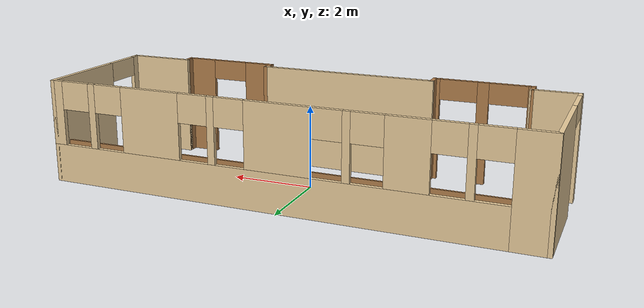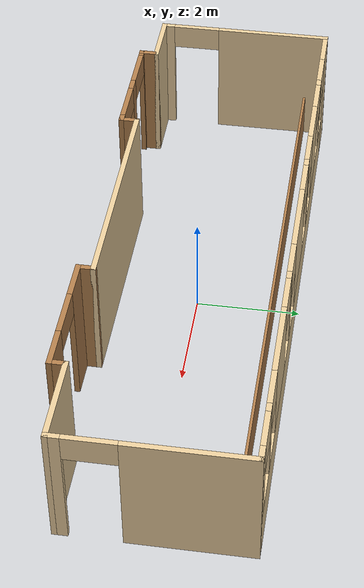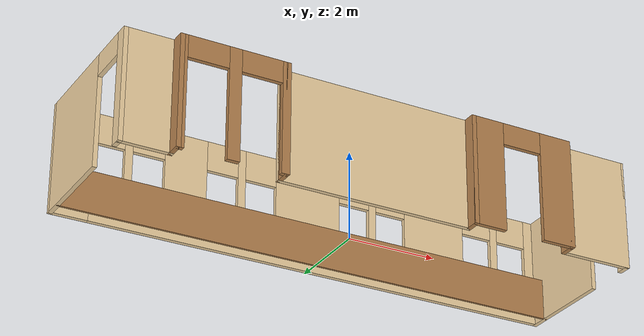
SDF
<?xml version='1.0'?>
<sdf version='1.6'>
  <model name='LawHall_Floor4.sdf'>
    <link name='Wall_0'>
      <pose frame=''>0 1.8775 0 0 -0 0</pose>
      <self_collide>0</self_collide>
      <kinematic>0</kinematic>
      <visual name='Wall_0_Visual_4'>
        <pose frame=''>-1.606 0 1.72 0 -0 0</pose>
        <geometry>
          <box>
            <size>0.178 0.1 1.56</size>
          </box>
        </geometry>
        <material>
          <script>
            <uri>file://media/materials/scripts/gazebo.material</uri>
            <name>Gazebo/Grey</name>
          </script>
          <ambient>0.921569 0.807843 0.615686 1</ambient>
          <diffuse>0.7 0.7 0.7 1</diffuse>
          <specular>0.01 0.01 0.01 1</specular>
          <emissive>0 0 0 1</emissive>
        </material>
        <cast_shadows>1</cast_shadows>
        <transparency>0</transparency>
      </visual>
      <visual name='Wall_0_Visual_15'>
        <pose frame=''>2.034 0 2.158 0 -0 0</pose>
        <geometry>
          <box>
            <size>0.73 0.1 0.684</size>
          </box>
        </geometry>
        <material>
          <script>
            <uri>file://media/materials/scripts/gazebo.material</uri>
            <name>Gazebo/Grey</name>
          </script>
          <ambient>0.921569 0.807843 0.615686 1</ambient>
          <diffuse>0.7 0.7 0.7 1</diffuse>
          <specular>0.01 0.01 0.01 1</specular>
          <emissive>0 0 0 1</emissive>
        </material>
        <cast_shadows>1</cast_shadows>
        <transparency>0</transparency>
      </visual>
      <visual name='Wall_0_Visual_0'>
        <pose frame=''>-5.4555 0 1.25 0 -0 0</pose>
        <geometry>
          <box>
            <size>0.841 0.1 2.5</size>
          </box>
        </geometry>
        <material>
          <script>
            <uri>file://media/materials/scripts/gazebo.material</uri>
            <name>Gazebo/Grey</name>
          </script>
          <ambient>0.921569 0.807843 0.615686 1</ambient>
          <diffuse>0.7 0.7 0.7 1</diffuse>
          <specular>0.01 0.01 0.01 1</specular>
          <emissive>0 0 0 1</emissive>
        </material>
        <cast_shadows>1</cast_shadows>
        <transparency>0</transparency>
      </visual>
      <visual name='Wall_0_Visual_7'>
        <pose frame=''>3.154 0 1.72 0 -0 0</pose>
        <geometry>
          <box>
            <size>1.51 0.1 1.56</size>
          </box>
        </geometry>
        <material>
          <script>
            <uri>file://media/materials/scripts/gazebo.material</uri>
            <name>Gazebo/Grey</name>
          </script>
          <ambient>0.921569 0.807843 0.615686 1</ambient>
          <diffuse>0.7 0.7 0.7 1</diffuse>
          <specular>0.01 0.01 0.01 1</specular>
          <emissive>0 0 0 1</emissive>
        </material>
        <cast_shadows>1</cast_shadows>
        <transparency>0</transparency>
      </visual>
      <visual name='Wall_0_Visual_17'>
        <pose frame=''>5.184 0 2.158 0 -0 0</pose>
        <geometry>
          <box>
            <size>0.73 0.1 0.684</size>
          </box>
        </geometry>
        <material>
          <script>
            <uri>file://media/materials/scripts/gazebo.material</uri>
            <name>Gazebo/Grey</name>
          </script>
          <ambient>0.921569 0.807843 0.615686 1</ambient>
          <diffuse>0.7 0.7 0.7 1</diffuse>
          <specular>0.01 0.01 0.01 1</specular>
          <emissive>0 0 0 1</emissive>
        </material>
        <cast_shadows>1</cast_shadows>
        <transparency>0</transparency>
      </visual>
      <visual name='Wall_0_Visual_6'>
        <pose frame=''>1.5805 0 1.72 0 -0 0</pose>
        <geometry>
          <box>
            <size>0.177 0.1 1.56</size>
          </box>
        </geometry>
        <material>
          <script>
            <uri>file://media/materials/scripts/gazebo.material</uri>
            <name>Gazebo/Grey</name>
          </script>
          <ambient>0.921569 0.807843 0.615686 1</ambient>
          <diffuse>0.7 0.7 0.7 1</diffuse>
          <specular>0.01 0.01 0.01 1</specular>
          <emissive>0 0 0 1</emissive>
        </material>
        <cast_shadows>1</cast_shadows>
        <transparency>0</transparency>
      </visual>
      <visual name='Wall_0_Visual_2'>
        <pose frame=''>-4.216 0 1.72 0 -0 0</pose>
        <geometry>
          <box>
            <size>0.178 0.1 1.56</size>
          </box>
        </geometry>
        <material>
          <script>
            <uri>file://media/materials/scripts/gazebo.material</uri>
            <name>Gazebo/Grey</name>
          </script>
          <ambient>0.921569 0.807843 0.615686 1</ambient>
          <diffuse>0.7 0.7 0.7 1</diffuse>
          <specular>0.01 0.01 0.01 1</specular>
          <emissive>0 0 0 1</emissive>
        </material>
        <cast_shadows>1</cast_shadows>
        <transparency>0</transparency>
      </visual>
      <visual name='Wall_0_Visual_9'>
        <pose frame=''>5.7125 0 1.72 0 -0 0</pose>
        <geometry>
          <box>
            <size>0.327 0.1 1.56</size>
          </box>
        </geometry>
        <material>
          <script>
            <uri>file://media/materials/scripts/gazebo.material</uri>
            <name>Gazebo/Grey</name>
          </script>
          <ambient>0.921569 0.807843 0.615686 1</ambient>
          <diffuse>0.7 0.7 0.7 1</diffuse>
          <specular>0.01 0.01 0.01 1</specular>
          <emissive>0 0 0 1</emissive>
        </material>
        <cast_shadows>1</cast_shadows>
        <transparency>0</transparency>
      </visual>
      <visual name='Wall_0_Visual_16'>
        <pose frame=''>4.274 0 2.158 0 -0 0</pose>
        <geometry>
          <box>
            <size>0.73 0.1 0.684</size>
          </box>
        </geometry>
        <material>
          <script>
            <uri>file://media/materials/scripts/gazebo.material</uri>
            <name>Gazebo/Grey</name>
          </script>
          <ambient>0.921569 0.807843 0.615686 1</ambient>
          <diffuse>0.7 0.7 0.7 1</diffuse>
          <specular>0.01 0.01 0.01 1</specular>
          <emissive>0 0 0 1</emissive>
        </material>
        <cast_shadows>1</cast_shadows>
        <transparency>0</transparency>
      </visual>
      <visual name='Wall_0_Visual_10'>
        <pose frame=''>-4.67 0 2.158 0 -0 0</pose>
        <geometry>
          <box>
            <size>0.73 0.1 0.684</size>
          </box>
        </geometry>
        <material>
          <script>
            <uri>file://media/materials/scripts/gazebo.material</uri>
            <name>Gazebo/Grey</name>
          </script>
          <ambient>0.921569 0.807843 0.615686 1</ambient>
          <diffuse>0.7 0.7 0.7 1</diffuse>
          <specular>0.01 0.01 0.01 1</specular>
          <emissive>0 0 0 1</emissive>
        </material>
        <cast_shadows>1</cast_shadows>
        <transparency>0</transparency>
      </visual>
      <visual name='Wall_0_Visual_11'>
        <pose frame=''>-3.762 0 2.158 0 -0 0</pose>
        <geometry>
          <box>
            <size>0.73 0.1 0.684</size>
          </box>
        </geometry>
        <material>
          <script>
            <uri>file://media/materials/scripts/gazebo.material</uri>
            <name>Gazebo/Grey</name>
          </script>
          <ambient>0.921569 0.807843 0.615686 1</ambient>
          <diffuse>0.7 0.7 0.7 1</diffuse>
          <specular>0.01 0.01 0.01 1</specular>
          <emissive>0 0 0 1</emissive>
        </material>
        <cast_shadows>1</cast_shadows>
        <transparency>0</transparency>
      </visual>
      <visual name='Wall_0_Visual_5'>
        <pose frame=''>-0.0125 0 1.72 0 -0 0</pose>
        <geometry>
          <box>
            <size>1.549 0.1 1.56</size>
          </box>
        </geometry>
        <material>
          <script>
            <uri>file://media/materials/scripts/gazebo.material</uri>
            <name>Gazebo/Grey</name>
          </script>
          <ambient>0.921569 0.807843 0.615686 1</ambient>
          <diffuse>0.7 0.7 0.7 1</diffuse>
          <specular>0.01 0.01 0.01 1</specular>
          <emissive>0 0 0 1</emissive>
        </material>
        <cast_shadows>1</cast_shadows>
        <transparency>0</transparency>
      </visual>
      <visual name='Wall_0_Visual_14'>
        <pose frame=''>1.127 0 2.158 0 -0 0</pose>
        <geometry>
          <box>
            <size>0.73 0.1 0.684</size>
          </box>
        </geometry>
        <material>
          <script>
            <uri>file://media/materials/scripts/gazebo.material</uri>
            <name>Gazebo/Grey</name>
          </script>
          <ambient>0.921569 0.807843 0.615686 1</ambient>
          <diffuse>0.7 0.7 0.7 1</diffuse>
          <specular>0.01 0.01 0.01 1</specular>
          <emissive>0 0 0 1</emissive>
        </material>
        <cast_shadows>1</cast_shadows>
        <transparency>0</transparency>
      </visual>
      <visual name='Wall_0_Visual_13'>
        <pose frame=''>-1.152 0 2.158 0 -0 0</pose>
        <geometry>
          <box>
            <size>0.73 0.1 0.684</size>
          </box>
        </geometry>
        <material>
          <script>
            <uri>file://media/materials/scripts/gazebo.material</uri>
            <name>Gazebo/Grey</name>
          </script>
          <ambient>0.921569 0.807843 0.615686 1</ambient>
          <diffuse>0.7 0.7 0.7 1</diffuse>
          <specular>0.01 0.01 0.01 1</specular>
          <emissive>0 0 0 1</emissive>
        </material>
        <cast_shadows>1</cast_shadows>
        <transparency>0</transparency>
      </visual>
      <visual name='Wall_0_Visual_12'>
        <pose frame=''>-2.06 0 2.158 0 -0 0</pose>
        <geometry>
          <box>
            <size>0.73 0.1 0.684</size>
          </box>
        </geometry>
        <material>
          <script>
            <uri>file://media/materials/scripts/gazebo.material</uri>
            <name>Gazebo/Grey</name>
          </script>
          <ambient>0.921569 0.807843 0.615686 1</ambient>
          <diffuse>0.7 0.7 0.7 1</diffuse>
          <specular>0.01 0.01 0.01 1</specular>
          <emissive>0 0 0 1</emissive>
        </material>
        <cast_shadows>1</cast_shadows>
        <transparency>0</transparency>
      </visual>
      <visual name='Wall_0_Visual_8'>
        <pose frame=''>4.729 0 1.72 0 -0 0</pose>
        <geometry>
          <box>
            <size>0.18 0.1 1.56</size>
          </box>
        </geometry>
        <material>
          <script>
            <uri>file://media/materials/scripts/gazebo.material</uri>
            <name>Gazebo/Grey</name>
          </script>
          <ambient>0.921569 0.807843 0.615686 1</ambient>
          <diffuse>0.7 0.7 0.7 1</diffuse>
          <specular>0.01 0.01 0.01 1</specular>
          <emissive>0 0 0 1</emissive>
        </material>
        <cast_shadows>1</cast_shadows>
        <transparency>0</transparency>
      </visual>
      <visual name='Wall_0_Visual_3'>
        <pose frame=''>-2.911 0 1.72 0 -0 0</pose>
        <geometry>
          <box>
            <size>0.972 0.1 1.56</size>
          </box>
        </geometry>
        <material>
          <script>
            <uri>file://media/materials/scripts/gazebo.material</uri>
            <name>Gazebo/Grey</name>
          </script>
          <ambient>0.921569 0.807843 0.615686 1</ambient>
          <diffuse>0.7 0.7 0.7 1</diffuse>
          <specular>0.01 0.01 0.01 1</specular>
          <emissive>0 0 0 1</emissive>
        </material>
        <cast_shadows>1</cast_shadows>
        <transparency>0</transparency>
      </visual>
      <visual name='Wall_0_Visual_1'>
        <pose frame=''>0.4205 0 0.47 0 -0 0</pose>
        <geometry>
          <box>
            <size>10.911 0.1 0.94</size>
          </box>
        </geometry>
        <material>
          <script>
            <uri>file://media/materials/scripts/gazebo.material</uri>
            <name>Gazebo/Grey</name>
          </script>
          <ambient>0.921569 0.807843 0.615686 1</ambient>
          <diffuse>0.7 0.7 0.7 1</diffuse>
          <specular>0.01 0.01 0.01 1</specular>
          <emissive>0 0 0 1</emissive>
        </material>
        <cast_shadows>1</cast_shadows>
        <transparency>0</transparency>
      </visual>
      <collision name='Wall_0_Collision_11'>
        <laser_retro>0</laser_retro>
        <max_contacts>10</max_contacts>
        <pose frame=''>-3.762 0 2.158 0 -0 0</pose>
        <geometry>
          <box>
            <size>0.73 0.1 0.684</size>
          </box>
        </geometry>
        <surface>
          <friction>
            <ode>
              <mu>1</mu>
              <mu2>1</mu2>
              <fdir1>0 0 0</fdir1>
              <slip1>0</slip1>
              <slip2>0</slip2>
            </ode>
            <torsional>
              <coefficient>1</coefficient>
              <patch_radius>0</patch_radius>
              <surface_radius>0</surface_radius>
              <use_patch_radius>1</use_patch_radius>
              <ode>
                <slip>0</slip>
              </ode>
            </torsional>
          </friction>
          <bounce>
            <restitution_coefficient>0</restitution_coefficient>
            <threshold>1e+06</threshold>
          </bounce>
          <contact>
            <collide_without_contact>0</collide_without_contact>
            <collide_without_contact_bitmask>1</collide_without_contact_bitmask>
            <collide_bitmask>1</collide_bitmask>
            <ode>
              <soft_cfm>0</soft_cfm>
              <soft_erp>0.2</soft_erp>
              <kp>1e+13</kp>
              <kd>1</kd>
              <max_vel>0.01</max_vel>
              <min_depth>0</min_depth>
            </ode>
            <bullet>
              <split_impulse>1</split_impulse>
              <split_impulse_penetration_threshold>-0.01</split_impulse_penetration_threshold>
              <soft_cfm>0</soft_cfm>
              <soft_erp>0.2</soft_erp>
              <kp>1e+13</kp>
              <kd>1</kd>
            </bullet>
          </contact>
        </surface>
      </collision>
      <collision name='Wall_0_Collision_7'>
        <laser_retro>0</laser_retro>
        <max_contacts>10</max_contacts>
        <pose frame=''>3.154 0 1.72 0 -0 0</pose>
        <geometry>
          <box>
            <size>1.51 0.1 1.56</size>
          </box>
        </geometry>
        <surface>
          <friction>
            <ode>
              <mu>1</mu>
              <mu2>1</mu2>
              <fdir1>0 0 0</fdir1>
              <slip1>0</slip1>
              <slip2>0</slip2>
            </ode>
            <torsional>
              <coefficient>1</coefficient>
              <patch_radius>0</patch_radius>
              <surface_radius>0</surface_radius>
              <use_patch_radius>1</use_patch_radius>
              <ode>
                <slip>0</slip>
              </ode>
            </torsional>
          </friction>
          <bounce>
            <restitution_coefficient>0</restitution_coefficient>
            <threshold>1e+06</threshold>
          </bounce>
          <contact>
            <collide_without_contact>0</collide_without_contact>
            <collide_without_contact_bitmask>1</collide_without_contact_bitmask>
            <collide_bitmask>1</collide_bitmask>
            <ode>
              <soft_cfm>0</soft_cfm>
              <soft_erp>0.2</soft_erp>
              <kp>1e+13</kp>
              <kd>1</kd>
              <max_vel>0.01</max_vel>
              <min_depth>0</min_depth>
            </ode>
            <bullet>
              <split_impulse>1</split_impulse>
              <split_impulse_penetration_threshold>-0.01</split_impulse_penetration_threshold>
              <soft_cfm>0</soft_cfm>
              <soft_erp>0.2</soft_erp>
              <kp>1e+13</kp>
              <kd>1</kd>
            </bullet>
          </contact>
        </surface>
      </collision>
      <collision name='Wall_0_Collision_14'>
        <laser_retro>0</laser_retro>
        <max_contacts>10</max_contacts>
        <pose frame=''>1.127 0 2.158 0 -0 0</pose>
        <geometry>
          <box>
            <size>0.73 0.1 0.684</size>
          </box>
        </geometry>
        <surface>
          <friction>
            <ode>
              <mu>1</mu>
              <mu2>1</mu2>
              <fdir1>0 0 0</fdir1>
              <slip1>0</slip1>
              <slip2>0</slip2>
            </ode>
            <torsional>
              <coefficient>1</coefficient>
              <patch_radius>0</patch_radius>
              <surface_radius>0</surface_radius>
              <use_patch_radius>1</use_patch_radius>
              <ode>
                <slip>0</slip>
              </ode>
            </torsional>
          </friction>
          <bounce>
            <restitution_coefficient>0</restitution_coefficient>
            <threshold>1e+06</threshold>
          </bounce>
          <contact>
            <collide_without_contact>0</collide_without_contact>
            <collide_without_contact_bitmask>1</collide_without_contact_bitmask>
            <collide_bitmask>1</collide_bitmask>
            <ode>
              <soft_cfm>0</soft_cfm>
              <soft_erp>0.2</soft_erp>
              <kp>1e+13</kp>
              <kd>1</kd>
              <max_vel>0.01</max_vel>
              <min_depth>0</min_depth>
            </ode>
            <bullet>
              <split_impulse>1</split_impulse>
              <split_impulse_penetration_threshold>-0.01</split_impulse_penetration_threshold>
              <soft_cfm>0</soft_cfm>
              <soft_erp>0.2</soft_erp>
              <kp>1e+13</kp>
              <kd>1</kd>
            </bullet>
          </contact>
        </surface>
      </collision>
      <collision name='Wall_0_Collision_5'>
        <laser_retro>0</laser_retro>
        <max_contacts>10</max_contacts>
        <pose frame=''>-0.0125 0 1.72 0 -0 0</pose>
        <geometry>
          <box>
            <size>1.549 0.1 1.56</size>
          </box>
        </geometry>
        <surface>
          <friction>
            <ode>
              <mu>1</mu>
              <mu2>1</mu2>
              <fdir1>0 0 0</fdir1>
              <slip1>0</slip1>
              <slip2>0</slip2>
            </ode>
            <torsional>
              <coefficient>1</coefficient>
              <patch_radius>0</patch_radius>
              <surface_radius>0</surface_radius>
              <use_patch_radius>1</use_patch_radius>
              <ode>
                <slip>0</slip>
              </ode>
            </torsional>
          </friction>
          <bounce>
            <restitution_coefficient>0</restitution_coefficient>
            <threshold>1e+06</threshold>
          </bounce>
          <contact>
            <collide_without_contact>0</collide_without_contact>
            <collide_without_contact_bitmask>1</collide_without_contact_bitmask>
            <collide_bitmask>1</collide_bitmask>
            <ode>
              <soft_cfm>0</soft_cfm>
              <soft_erp>0.2</soft_erp>
              <kp>1e+13</kp>
              <kd>1</kd>
              <max_vel>0.01</max_vel>
              <min_depth>0</min_depth>
            </ode>
            <bullet>
              <split_impulse>1</split_impulse>
              <split_impulse_penetration_threshold>-0.01</split_impulse_penetration_threshold>
              <soft_cfm>0</soft_cfm>
              <soft_erp>0.2</soft_erp>
              <kp>1e+13</kp>
              <kd>1</kd>
            </bullet>
          </contact>
        </surface>
      </collision>
      <collision name='Wall_0_Collision_9'>
        <laser_retro>0</laser_retro>
        <max_contacts>10</max_contacts>
        <pose frame=''>5.7125 0 1.72 0 -0 0</pose>
        <geometry>
          <box>
            <size>0.327 0.1 1.56</size>
          </box>
        </geometry>
        <surface>
          <friction>
            <ode>
              <mu>1</mu>
              <mu2>1</mu2>
              <fdir1>0 0 0</fdir1>
              <slip1>0</slip1>
              <slip2>0</slip2>
            </ode>
            <torsional>
              <coefficient>1</coefficient>
              <patch_radius>0</patch_radius>
              <surface_radius>0</surface_radius>
              <use_patch_radius>1</use_patch_radius>
              <ode>
                <slip>0</slip>
              </ode>
            </torsional>
          </friction>
          <bounce>
            <restitution_coefficient>0</restitution_coefficient>
            <threshold>1e+06</threshold>
          </bounce>
          <contact>
            <collide_without_contact>0</collide_without_contact>
            <collide_without_contact_bitmask>1</collide_without_contact_bitmask>
            <collide_bitmask>1</collide_bitmask>
            <ode>
              <soft_cfm>0</soft_cfm>
              <soft_erp>0.2</soft_erp>
              <kp>1e+13</kp>
              <kd>1</kd>
              <max_vel>0.01</max_vel>
              <min_depth>0</min_depth>
            </ode>
            <bullet>
              <split_impulse>1</split_impulse>
              <split_impulse_penetration_threshold>-0.01</split_impulse_penetration_threshold>
              <soft_cfm>0</soft_cfm>
              <soft_erp>0.2</soft_erp>
              <kp>1e+13</kp>
              <kd>1</kd>
            </bullet>
          </contact>
        </surface>
      </collision>
      <collision name='Wall_0_Collision_2'>
        <laser_retro>0</laser_retro>
        <max_contacts>10</max_contacts>
        <pose frame=''>-4.216 0 1.72 0 -0 0</pose>
        <geometry>
          <box>
            <size>0.178 0.1 1.56</size>
          </box>
        </geometry>
        <surface>
          <friction>
            <ode>
              <mu>1</mu>
              <mu2>1</mu2>
              <fdir1>0 0 0</fdir1>
              <slip1>0</slip1>
              <slip2>0</slip2>
            </ode>
            <torsional>
              <coefficient>1</coefficient>
              <patch_radius>0</patch_radius>
              <surface_radius>0</surface_radius>
              <use_patch_radius>1</use_patch_radius>
              <ode>
                <slip>0</slip>
              </ode>
            </torsional>
          </friction>
          <bounce>
            <restitution_coefficient>0</restitution_coefficient>
            <threshold>1e+06</threshold>
          </bounce>
          <contact>
            <collide_without_contact>0</collide_without_contact>
            <collide_without_contact_bitmask>1</collide_without_contact_bitmask>
            <collide_bitmask>1</collide_bitmask>
            <ode>
              <soft_cfm>0</soft_cfm>
              <soft_erp>0.2</soft_erp>
              <kp>1e+13</kp>
              <kd>1</kd>
              <max_vel>0.01</max_vel>
              <min_depth>0</min_depth>
            </ode>
            <bullet>
              <split_impulse>1</split_impulse>
              <split_impulse_penetration_threshold>-0.01</split_impulse_penetration_threshold>
              <soft_cfm>0</soft_cfm>
              <soft_erp>0.2</soft_erp>
              <kp>1e+13</kp>
              <kd>1</kd>
            </bullet>
          </contact>
        </surface>
      </collision>
      <collision name='Wall_0_Collision_3'>
        <laser_retro>0</laser_retro>
        <max_contacts>10</max_contacts>
        <pose frame=''>-2.911 0 1.72 0 -0 0</pose>
        <geometry>
          <box>
            <size>0.972 0.1 1.56</size>
          </box>
        </geometry>
        <surface>
          <friction>
            <ode>
              <mu>1</mu>
              <mu2>1</mu2>
              <fdir1>0 0 0</fdir1>
              <slip1>0</slip1>
              <slip2>0</slip2>
            </ode>
            <torsional>
              <coefficient>1</coefficient>
              <patch_radius>0</patch_radius>
              <surface_radius>0</surface_radius>
              <use_patch_radius>1</use_patch_radius>
              <ode>
                <slip>0</slip>
              </ode>
            </torsional>
          </friction>
          <bounce>
            <restitution_coefficient>0</restitution_coefficient>
            <threshold>1e+06</threshold>
          </bounce>
          <contact>
            <collide_without_contact>0</collide_without_contact>
            <collide_without_contact_bitmask>1</collide_without_contact_bitmask>
            <collide_bitmask>1</collide_bitmask>
            <ode>
              <soft_cfm>0</soft_cfm>
              <soft_erp>0.2</soft_erp>
              <kp>1e+13</kp>
              <kd>1</kd>
              <max_vel>0.01</max_vel>
              <min_depth>0</min_depth>
            </ode>
            <bullet>
              <split_impulse>1</split_impulse>
              <split_impulse_penetration_threshold>-0.01</split_impulse_penetration_threshold>
              <soft_cfm>0</soft_cfm>
              <soft_erp>0.2</soft_erp>
              <kp>1e+13</kp>
              <kd>1</kd>
            </bullet>
          </contact>
        </surface>
      </collision>
      <collision name='Wall_0_Collision_6'>
        <laser_retro>0</laser_retro>
        <max_contacts>10</max_contacts>
        <pose frame=''>1.5805 0 1.72 0 -0 0</pose>
        <geometry>
          <box>
            <size>0.177 0.1 1.56</size>
          </box>
        </geometry>
        <surface>
          <friction>
            <ode>
              <mu>1</mu>
              <mu2>1</mu2>
              <fdir1>0 0 0</fdir1>
              <slip1>0</slip1>
              <slip2>0</slip2>
            </ode>
            <torsional>
              <coefficient>1</coefficient>
              <patch_radius>0</patch_radius>
              <surface_radius>0</surface_radius>
              <use_patch_radius>1</use_patch_radius>
              <ode>
                <slip>0</slip>
              </ode>
            </torsional>
          </friction>
          <bounce>
            <restitution_coefficient>0</restitution_coefficient>
            <threshold>1e+06</threshold>
          </bounce>
          <contact>
            <collide_without_contact>0</collide_without_contact>
            <collide_without_contact_bitmask>1</collide_without_contact_bitmask>
            <collide_bitmask>1</collide_bitmask>
            <ode>
              <soft_cfm>0</soft_cfm>
              <soft_erp>0.2</soft_erp>
              <kp>1e+13</kp>
              <kd>1</kd>
              <max_vel>0.01</max_vel>
              <min_depth>0</min_depth>
            </ode>
            <bullet>
              <split_impulse>1</split_impulse>
              <split_impulse_penetration_threshold>-0.01</split_impulse_penetration_threshold>
              <soft_cfm>0</soft_cfm>
              <soft_erp>0.2</soft_erp>
              <kp>1e+13</kp>
              <kd>1</kd>
            </bullet>
          </contact>
        </surface>
      </collision>
      <collision name='Wall_0_Collision_13'>
        <laser_retro>0</laser_retro>
        <max_contacts>10</max_contacts>
        <pose frame=''>-1.152 0 2.158 0 -0 0</pose>
        <geometry>
          <box>
            <size>0.73 0.1 0.684</size>
          </box>
        </geometry>
        <surface>
          <friction>
            <ode>
              <mu>1</mu>
              <mu2>1</mu2>
              <fdir1>0 0 0</fdir1>
              <slip1>0</slip1>
              <slip2>0</slip2>
            </ode>
            <torsional>
              <coefficient>1</coefficient>
              <patch_radius>0</patch_radius>
              <surface_radius>0</surface_radius>
              <use_patch_radius>1</use_patch_radius>
              <ode>
                <slip>0</slip>
              </ode>
            </torsional>
          </friction>
          <bounce>
            <restitution_coefficient>0</restitution_coefficient>
            <threshold>1e+06</threshold>
          </bounce>
          <contact>
            <collide_without_contact>0</collide_without_contact>
            <collide_without_contact_bitmask>1</collide_without_contact_bitmask>
            <collide_bitmask>1</collide_bitmask>
            <ode>
              <soft_cfm>0</soft_cfm>
              <soft_erp>0.2</soft_erp>
              <kp>1e+13</kp>
              <kd>1</kd>
              <max_vel>0.01</max_vel>
              <min_depth>0</min_depth>
            </ode>
            <bullet>
              <split_impulse>1</split_impulse>
              <split_impulse_penetration_threshold>-0.01</split_impulse_penetration_threshold>
              <soft_cfm>0</soft_cfm>
              <soft_erp>0.2</soft_erp>
              <kp>1e+13</kp>
              <kd>1</kd>
            </bullet>
          </contact>
        </surface>
      </collision>
      <collision name='Wall_0_Collision_15'>
        <laser_retro>0</laser_retro>
        <max_contacts>10</max_contacts>
        <pose frame=''>2.034 0 2.158 0 -0 0</pose>
        <geometry>
          <box>
            <size>0.73 0.1 0.684</size>
          </box>
        </geometry>
        <surface>
          <friction>
            <ode>
              <mu>1</mu>
              <mu2>1</mu2>
              <fdir1>0 0 0</fdir1>
              <slip1>0</slip1>
              <slip2>0</slip2>
            </ode>
            <torsional>
              <coefficient>1</coefficient>
              <patch_radius>0</patch_radius>
              <surface_radius>0</surface_radius>
              <use_patch_radius>1</use_patch_radius>
              <ode>
                <slip>0</slip>
              </ode>
            </torsional>
          </friction>
          <bounce>
            <restitution_coefficient>0</restitution_coefficient>
            <threshold>1e+06</threshold>
          </bounce>
          <contact>
            <collide_without_contact>0</collide_without_contact>
            <collide_without_contact_bitmask>1</collide_without_contact_bitmask>
            <collide_bitmask>1</collide_bitmask>
            <ode>
              <soft_cfm>0</soft_cfm>
              <soft_erp>0.2</soft_erp>
              <kp>1e+13</kp>
              <kd>1</kd>
              <max_vel>0.01</max_vel>
              <min_depth>0</min_depth>
            </ode>
            <bullet>
              <split_impulse>1</split_impulse>
              <split_impulse_penetration_threshold>-0.01</split_impulse_penetration_threshold>
              <soft_cfm>0</soft_cfm>
              <soft_erp>0.2</soft_erp>
              <kp>1e+13</kp>
              <kd>1</kd>
            </bullet>
          </contact>
        </surface>
      </collision>
      <collision name='Wall_0_Collision_1'>
        <laser_retro>0</laser_retro>
        <max_contacts>10</max_contacts>
        <pose frame=''>0.4205 0 0.47 0 -0 0</pose>
        <geometry>
          <box>
            <size>10.911 0.1 0.94</size>
          </box>
        </geometry>
        <surface>
          <friction>
            <ode>
              <mu>1</mu>
              <mu2>1</mu2>
              <fdir1>0 0 0</fdir1>
              <slip1>0</slip1>
              <slip2>0</slip2>
            </ode>
            <torsional>
              <coefficient>1</coefficient>
              <patch_radius>0</patch_radius>
              <surface_radius>0</surface_radius>
              <use_patch_radius>1</use_patch_radius>
              <ode>
                <slip>0</slip>
              </ode>
            </torsional>
          </friction>
          <bounce>
            <restitution_coefficient>0</restitution_coefficient>
            <threshold>1e+06</threshold>
          </bounce>
          <contact>
            <collide_without_contact>0</collide_without_contact>
            <collide_without_contact_bitmask>1</collide_without_contact_bitmask>
            <collide_bitmask>1</collide_bitmask>
            <ode>
              <soft_cfm>0</soft_cfm>
              <soft_erp>0.2</soft_erp>
              <kp>1e+13</kp>
              <kd>1</kd>
              <max_vel>0.01</max_vel>
              <min_depth>0</min_depth>
            </ode>
            <bullet>
              <split_impulse>1</split_impulse>
              <split_impulse_penetration_threshold>-0.01</split_impulse_penetration_threshold>
              <soft_cfm>0</soft_cfm>
              <soft_erp>0.2</soft_erp>
              <kp>1e+13</kp>
              <kd>1</kd>
            </bullet>
          </contact>
        </surface>
      </collision>
      <collision name='Wall_0_Collision_16'>
        <laser_retro>0</laser_retro>
        <max_contacts>10</max_contacts>
        <pose frame=''>4.274 0 2.158 0 -0 0</pose>
        <geometry>
          <box>
            <size>0.73 0.1 0.684</size>
          </box>
        </geometry>
        <surface>
          <friction>
            <ode>
              <mu>1</mu>
              <mu2>1</mu2>
              <fdir1>0 0 0</fdir1>
              <slip1>0</slip1>
              <slip2>0</slip2>
            </ode>
            <torsional>
              <coefficient>1</coefficient>
              <patch_radius>0</patch_radius>
              <surface_radius>0</surface_radius>
              <use_patch_radius>1</use_patch_radius>
              <ode>
                <slip>0</slip>
              </ode>
            </torsional>
          </friction>
          <bounce>
            <restitution_coefficient>0</restitution_coefficient>
            <threshold>1e+06</threshold>
          </bounce>
          <contact>
            <collide_without_contact>0</collide_without_contact>
            <collide_without_contact_bitmask>1</collide_without_contact_bitmask>
            <collide_bitmask>1</collide_bitmask>
            <ode>
              <soft_cfm>0</soft_cfm>
              <soft_erp>0.2</soft_erp>
              <kp>1e+13</kp>
              <kd>1</kd>
              <max_vel>0.01</max_vel>
              <min_depth>0</min_depth>
            </ode>
            <bullet>
              <split_impulse>1</split_impulse>
              <split_impulse_penetration_threshold>-0.01</split_impulse_penetration_threshold>
              <soft_cfm>0</soft_cfm>
              <soft_erp>0.2</soft_erp>
              <kp>1e+13</kp>
              <kd>1</kd>
            </bullet>
          </contact>
        </surface>
      </collision>
      <collision name='Wall_0_Collision_12'>
        <laser_retro>0</laser_retro>
        <max_contacts>10</max_contacts>
        <pose frame=''>-2.06 0 2.158 0 -0 0</pose>
        <geometry>
          <box>
            <size>0.73 0.1 0.684</size>
          </box>
        </geometry>
        <surface>
          <friction>
            <ode>
              <mu>1</mu>
              <mu2>1</mu2>
              <fdir1>0 0 0</fdir1>
              <slip1>0</slip1>
              <slip2>0</slip2>
            </ode>
            <torsional>
              <coefficient>1</coefficient>
              <patch_radius>0</patch_radius>
              <surface_radius>0</surface_radius>
              <use_patch_radius>1</use_patch_radius>
              <ode>
                <slip>0</slip>
              </ode>
            </torsional>
          </friction>
          <bounce>
            <restitution_coefficient>0</restitution_coefficient>
            <threshold>1e+06</threshold>
          </bounce>
          <contact>
            <collide_without_contact>0</collide_without_contact>
            <collide_without_contact_bitmask>1</collide_without_contact_bitmask>
            <collide_bitmask>1</collide_bitmask>
            <ode>
              <soft_cfm>0</soft_cfm>
              <soft_erp>0.2</soft_erp>
              <kp>1e+13</kp>
              <kd>1</kd>
              <max_vel>0.01</max_vel>
              <min_depth>0</min_depth>
            </ode>
            <bullet>
              <split_impulse>1</split_impulse>
              <split_impulse_penetration_threshold>-0.01</split_impulse_penetration_threshold>
              <soft_cfm>0</soft_cfm>
              <soft_erp>0.2</soft_erp>
              <kp>1e+13</kp>
              <kd>1</kd>
            </bullet>
          </contact>
        </surface>
      </collision>
      <collision name='Wall_0_Collision_4'>
        <laser_retro>0</laser_retro>
        <max_contacts>10</max_contacts>
        <pose frame=''>-1.606 0 1.72 0 -0 0</pose>
        <geometry>
          <box>
            <size>0.178 0.1 1.56</size>
          </box>
        </geometry>
        <surface>
          <friction>
            <ode>
              <mu>1</mu>
              <mu2>1</mu2>
              <fdir1>0 0 0</fdir1>
              <slip1>0</slip1>
              <slip2>0</slip2>
            </ode>
            <torsional>
              <coefficient>1</coefficient>
              <patch_radius>0</patch_radius>
              <surface_radius>0</surface_radius>
              <use_patch_radius>1</use_patch_radius>
              <ode>
                <slip>0</slip>
              </ode>
            </torsional>
          </friction>
          <bounce>
            <restitution_coefficient>0</restitution_coefficient>
            <threshold>1e+06</threshold>
          </bounce>
          <contact>
            <collide_without_contact>0</collide_without_contact>
            <collide_without_contact_bitmask>1</collide_without_contact_bitmask>
            <collide_bitmask>1</collide_bitmask>
            <ode>
              <soft_cfm>0</soft_cfm>
              <soft_erp>0.2</soft_erp>
              <kp>1e+13</kp>
              <kd>1</kd>
              <max_vel>0.01</max_vel>
              <min_depth>0</min_depth>
            </ode>
            <bullet>
              <split_impulse>1</split_impulse>
              <split_impulse_penetration_threshold>-0.01</split_impulse_penetration_threshold>
              <soft_cfm>0</soft_cfm>
              <soft_erp>0.2</soft_erp>
              <kp>1e+13</kp>
              <kd>1</kd>
            </bullet>
          </contact>
        </surface>
      </collision>
      <collision name='Wall_0_Collision_17'>
        <laser_retro>0</laser_retro>
        <max_contacts>10</max_contacts>
        <pose frame=''>5.184 0 2.158 0 -0 0</pose>
        <geometry>
          <box>
            <size>0.73 0.1 0.684</size>
          </box>
        </geometry>
        <surface>
          <friction>
            <ode>
              <mu>1</mu>
              <mu2>1</mu2>
              <fdir1>0 0 0</fdir1>
              <slip1>0</slip1>
              <slip2>0</slip2>
            </ode>
            <torsional>
              <coefficient>1</coefficient>
              <patch_radius>0</patch_radius>
              <surface_radius>0</surface_radius>
              <use_patch_radius>1</use_patch_radius>
              <ode>
                <slip>0</slip>
              </ode>
            </torsional>
          </friction>
          <bounce>
            <restitution_coefficient>0</restitution_coefficient>
            <threshold>1e+06</threshold>
          </bounce>
          <contact>
            <collide_without_contact>0</collide_without_contact>
            <collide_without_contact_bitmask>1</collide_without_contact_bitmask>
            <collide_bitmask>1</collide_bitmask>
            <ode>
              <soft_cfm>0</soft_cfm>
              <soft_erp>0.2</soft_erp>
              <kp>1e+13</kp>
              <kd>1</kd>
              <max_vel>0.01</max_vel>
              <min_depth>0</min_depth>
            </ode>
            <bullet>
              <split_impulse>1</split_impulse>
              <split_impulse_penetration_threshold>-0.01</split_impulse_penetration_threshold>
              <soft_cfm>0</soft_cfm>
              <soft_erp>0.2</soft_erp>
              <kp>1e+13</kp>
              <kd>1</kd>
            </bullet>
          </contact>
        </surface>
      </collision>
      <collision name='Wall_0_Collision_8'>
        <laser_retro>0</laser_retro>
        <max_contacts>10</max_contacts>
        <pose frame=''>4.729 0 1.72 0 -0 0</pose>
        <geometry>
          <box>
            <size>0.18 0.1 1.56</size>
          </box>
        </geometry>
        <surface>
          <friction>
            <ode>
              <mu>1</mu>
              <mu2>1</mu2>
              <fdir1>0 0 0</fdir1>
              <slip1>0</slip1>
              <slip2>0</slip2>
            </ode>
            <torsional>
              <coefficient>1</coefficient>
              <patch_radius>0</patch_radius>
              <surface_radius>0</surface_radius>
              <use_patch_radius>1</use_patch_radius>
              <ode>
                <slip>0</slip>
              </ode>
            </torsional>
          </friction>
          <bounce>
            <restitution_coefficient>0</restitution_coefficient>
            <threshold>1e+06</threshold>
          </bounce>
          <contact>
            <collide_without_contact>0</collide_without_contact>
            <collide_without_contact_bitmask>1</collide_without_contact_bitmask>
            <collide_bitmask>1</collide_bitmask>
            <ode>
              <soft_cfm>0</soft_cfm>
              <soft_erp>0.2</soft_erp>
              <kp>1e+13</kp>
              <kd>1</kd>
              <max_vel>0.01</max_vel>
              <min_depth>0</min_depth>
            </ode>
            <bullet>
              <split_impulse>1</split_impulse>
              <split_impulse_penetration_threshold>-0.01</split_impulse_penetration_threshold>
              <soft_cfm>0</soft_cfm>
              <soft_erp>0.2</soft_erp>
              <kp>1e+13</kp>
              <kd>1</kd>
            </bullet>
          </contact>
        </surface>
      </collision>
      <collision name='Wall_0_Collision_0'>
        <laser_retro>0</laser_retro>
        <max_contacts>10</max_contacts>
        <pose frame=''>-5.4555 0 1.25 0 -0 0</pose>
        <geometry>
          <box>
            <size>0.841 0.1 2.5</size>
          </box>
        </geometry>
        <surface>
          <friction>
            <ode>
              <mu>1</mu>
              <mu2>1</mu2>
              <fdir1>0 0 0</fdir1>
              <slip1>0</slip1>
              <slip2>0</slip2>
            </ode>
            <torsional>
              <coefficient>1</coefficient>
              <patch_radius>0</patch_radius>
              <surface_radius>0</surface_radius>
              <use_patch_radius>1</use_patch_radius>
              <ode>
                <slip>0</slip>
              </ode>
            </torsional>
          </friction>
          <bounce>
            <restitution_coefficient>0</restitution_coefficient>
            <threshold>1e+06</threshold>
          </bounce>
          <contact>
            <collide_without_contact>0</collide_without_contact>
            <collide_without_contact_bitmask>1</collide_without_contact_bitmask>
            <collide_bitmask>1</collide_bitmask>
            <ode>
              <soft_cfm>0</soft_cfm>
              <soft_erp>0.2</soft_erp>
              <kp>1e+13</kp>
              <kd>1</kd>
              <max_vel>0.01</max_vel>
              <min_depth>0</min_depth>
            </ode>
            <bullet>
              <split_impulse>1</split_impulse>
              <split_impulse_penetration_threshold>-0.01</split_impulse_penetration_threshold>
              <soft_cfm>0</soft_cfm>
              <soft_erp>0.2</soft_erp>
              <kp>1e+13</kp>
              <kd>1</kd>
            </bullet>
          </contact>
        </surface>
      </collision>
      <collision name='Wall_0_Collision_10'>
        <laser_retro>0</laser_retro>
        <max_contacts>10</max_contacts>
        <pose frame=''>-4.67 0 2.158 0 -0 0</pose>
        <geometry>
          <box>
            <size>0.73 0.1 0.684</size>
          </box>
        </geometry>
        <surface>
          <friction>
            <ode>
              <mu>1</mu>
              <mu2>1</mu2>
              <fdir1>0 0 0</fdir1>
              <slip1>0</slip1>
              <slip2>0</slip2>
            </ode>
            <torsional>
              <coefficient>1</coefficient>
              <patch_radius>0</patch_radius>
              <surface_radius>0</surface_radius>
              <use_patch_radius>1</use_patch_radius>
              <ode>
                <slip>0</slip>
              </ode>
            </torsional>
          </friction>
          <bounce>
            <restitution_coefficient>0</restitution_coefficient>
            <threshold>1e+06</threshold>
          </bounce>
          <contact>
            <collide_without_contact>0</collide_without_contact>
            <collide_without_contact_bitmask>1</collide_without_contact_bitmask>
            <collide_bitmask>1</collide_bitmask>
            <ode>
              <soft_cfm>0</soft_cfm>
              <soft_erp>0.2</soft_erp>
              <kp>1e+13</kp>
              <kd>1</kd>
              <max_vel>0.01</max_vel>
              <min_depth>0</min_depth>
            </ode>
            <bullet>
              <split_impulse>1</split_impulse>
              <split_impulse_penetration_threshold>-0.01</split_impulse_penetration_threshold>
              <soft_cfm>0</soft_cfm>
              <soft_erp>0.2</soft_erp>
              <kp>1e+13</kp>
              <kd>1</kd>
            </bullet>
          </contact>
        </surface>
      </collision>
    </link>
    <link name='Wall_12'>
      <pose frame=''>4.251 -1.712 0 0 0 -1.5708</pose>
      <self_collide>0</self_collide>
      <kinematic>0</kinematic>
      <visual name='Wall_12_Visual'>
        <pose frame=''>0 0 1.25 0 -0 0</pose>
        <geometry>
          <box>
            <size>0.379 0.1 2.5</size>
          </box>
        </geometry>
        <material>
          <script>
            <uri>file://media/materials/scripts/gazebo.material</uri>
            <name>Gazebo/Wood</name>
          </script>
          <ambient>1 1 1 1</ambient>
          <diffuse>1 1 1 1</diffuse>
          <specular>0.2 0.2 0.2 1</specular>
          <emissive>0 0 0 1</emissive>
        </material>
        <cast_shadows>1</cast_shadows>
        <transparency>0</transparency>
      </visual>
      <collision name='Wall_12_Collision'>
        <laser_retro>0</laser_retro>
        <max_contacts>10</max_contacts>
        <pose frame=''>0 0 1.25 0 -0 0</pose>
        <geometry>
          <box>
            <size>0.379 0.1 2.5</size>
          </box>
        </geometry>
        <surface>
          <friction>
            <ode>
              <mu>1</mu>
              <mu2>1</mu2>
              <fdir1>0 0 0</fdir1>
              <slip1>0</slip1>
              <slip2>0</slip2>
            </ode>
            <torsional>
              <coefficient>1</coefficient>
              <patch_radius>0</patch_radius>
              <surface_radius>0</surface_radius>
              <use_patch_radius>1</use_patch_radius>
              <ode>
                <slip>0</slip>
              </ode>
            </torsional>
          </friction>
          <bounce>
            <restitution_coefficient>0</restitution_coefficient>
            <threshold>1e+06</threshold>
          </bounce>
          <contact>
            <collide_without_contact>0</collide_without_contact>
            <collide_without_contact_bitmask>1</collide_without_contact_bitmask>
            <collide_bitmask>1</collide_bitmask>
            <ode>
              <soft_cfm>0</soft_cfm>
              <soft_erp>0.2</soft_erp>
              <kp>1e+13</kp>
              <kd>1</kd>
              <max_vel>0.01</max_vel>
              <min_depth>0</min_depth>
            </ode>
            <bullet>
              <split_impulse>1</split_impulse>
              <split_impulse_penetration_threshold>-0.01</split_impulse_penetration_threshold>
              <soft_cfm>0</soft_cfm>
              <soft_erp>0.2</soft_erp>
              <kp>1e+13</kp>
              <kd>1</kd>
            </bullet>
          </contact>
        </surface>
      </collision>
    </link>
    <link name='Wall_14'>
      <pose frame=''>3.078 -1.8515 0 0 -0 3.14159</pose>
      <self_collide>0</self_collide>
      <kinematic>0</kinematic>
      <visual name='Wall_14_Visual_0'>
        <pose frame=''>-0.836227 0 1.25 0 -0 0</pose>
        <geometry>
          <box>
            <size>0.773547 0.1 2.5</size>
          </box>
        </geometry>
        <material>
          <script>
            <uri>file://media/materials/scripts/gazebo.material</uri>
            <name>Gazebo/Wood</name>
          </script>
          <ambient>1 1 1 1</ambient>
          <diffuse>1 1 1 1</diffuse>
          <specular>0.2 0.2 0.2 1</specular>
          <emissive>0 0 0 1</emissive>
        </material>
        <cast_shadows>1</cast_shadows>
        <transparency>0</transparency>
      </visual>
      <visual name='Wall_14_Visual_2'>
        <pose frame=''>0.005547 0 2.25 0 -0 0</pose>
        <geometry>
          <box>
            <size>0.91 0.1 0.5</size>
          </box>
        </geometry>
        <material>
          <script>
            <uri>file://media/materials/scripts/gazebo.material</uri>
            <name>Gazebo/Wood</name>
          </script>
          <ambient>1 1 1 1</ambient>
          <diffuse>1 1 1 1</diffuse>
          <specular>0.2 0.2 0.2 1</specular>
          <emissive>0 0 0 1</emissive>
        </material>
        <cast_shadows>1</cast_shadows>
        <transparency>0</transparency>
      </visual>
      <visual name='Wall_14_Visual_1'>
        <pose frame=''>0.841773 0 1.25 0 -0 0</pose>
        <geometry>
          <box>
            <size>0.762453 0.1 2.5</size>
          </box>
        </geometry>
        <material>
          <script>
            <uri>file://media/materials/scripts/gazebo.material</uri>
            <name>Gazebo/Wood</name>
          </script>
          <ambient>1 1 1 1</ambient>
          <diffuse>1 1 1 1</diffuse>
          <specular>0.2 0.2 0.2 1</specular>
          <emissive>0 0 0 1</emissive>
        </material>
        <cast_shadows>1</cast_shadows>
        <transparency>0</transparency>
      </visual>
      <collision name='Wall_14_Collision_1'>
        <laser_retro>0</laser_retro>
        <max_contacts>10</max_contacts>
        <pose frame=''>0.841773 0 1.25 0 -0 0</pose>
        <geometry>
          <box>
            <size>0.762453 0.1 2.5</size>
          </box>
        </geometry>
        <surface>
          <friction>
            <ode>
              <mu>1</mu>
              <mu2>1</mu2>
              <fdir1>0 0 0</fdir1>
              <slip1>0</slip1>
              <slip2>0</slip2>
            </ode>
            <torsional>
              <coefficient>1</coefficient>
              <patch_radius>0</patch_radius>
              <surface_radius>0</surface_radius>
              <use_patch_radius>1</use_patch_radius>
              <ode>
                <slip>0</slip>
              </ode>
            </torsional>
          </friction>
          <bounce>
            <restitution_coefficient>0</restitution_coefficient>
            <threshold>1e+06</threshold>
          </bounce>
          <contact>
            <collide_without_contact>0</collide_without_contact>
            <collide_without_contact_bitmask>1</collide_without_contact_bitmask>
            <collide_bitmask>1</collide_bitmask>
            <ode>
              <soft_cfm>0</soft_cfm>
              <soft_erp>0.2</soft_erp>
              <kp>1e+13</kp>
              <kd>1</kd>
              <max_vel>0.01</max_vel>
              <min_depth>0</min_depth>
            </ode>
            <bullet>
              <split_impulse>1</split_impulse>
              <split_impulse_penetration_threshold>-0.01</split_impulse_penetration_threshold>
              <soft_cfm>0</soft_cfm>
              <soft_erp>0.2</soft_erp>
              <kp>1e+13</kp>
              <kd>1</kd>
            </bullet>
          </contact>
        </surface>
      </collision>
      <collision name='Wall_14_Collision_2'>
        <laser_retro>0</laser_retro>
        <max_contacts>10</max_contacts>
        <pose frame=''>0.005547 0 2.25 0 -0 0</pose>
        <geometry>
          <box>
            <size>0.91 0.1 0.5</size>
          </box>
        </geometry>
        <surface>
          <friction>
            <ode>
              <mu>1</mu>
              <mu2>1</mu2>
              <fdir1>0 0 0</fdir1>
              <slip1>0</slip1>
              <slip2>0</slip2>
            </ode>
            <torsional>
              <coefficient>1</coefficient>
              <patch_radius>0</patch_radius>
              <surface_radius>0</surface_radius>
              <use_patch_radius>1</use_patch_radius>
              <ode>
                <slip>0</slip>
              </ode>
            </torsional>
          </friction>
          <bounce>
            <restitution_coefficient>0</restitution_coefficient>
            <threshold>1e+06</threshold>
          </bounce>
          <contact>
            <collide_without_contact>0</collide_without_contact>
            <collide_without_contact_bitmask>1</collide_without_contact_bitmask>
            <collide_bitmask>1</collide_bitmask>
            <ode>
              <soft_cfm>0</soft_cfm>
              <soft_erp>0.2</soft_erp>
              <kp>1e+13</kp>
              <kd>1</kd>
              <max_vel>0.01</max_vel>
              <min_depth>0</min_depth>
            </ode>
            <bullet>
              <split_impulse>1</split_impulse>
              <split_impulse_penetration_threshold>-0.01</split_impulse_penetration_threshold>
              <soft_cfm>0</soft_cfm>
              <soft_erp>0.2</soft_erp>
              <kp>1e+13</kp>
              <kd>1</kd>
            </bullet>
          </contact>
        </surface>
      </collision>
      <collision name='Wall_14_Collision_0'>
        <laser_retro>0</laser_retro>
        <max_contacts>10</max_contacts>
        <pose frame=''>-0.836227 0 1.25 0 -0 0</pose>
        <geometry>
          <box>
            <size>0.773547 0.1 2.5</size>
          </box>
        </geometry>
        <surface>
          <friction>
            <ode>
              <mu>1</mu>
              <mu2>1</mu2>
              <fdir1>0 0 0</fdir1>
              <slip1>0</slip1>
              <slip2>0</slip2>
            </ode>
            <torsional>
              <coefficient>1</coefficient>
              <patch_radius>0</patch_radius>
              <surface_radius>0</surface_radius>
              <use_patch_radius>1</use_patch_radius>
              <ode>
                <slip>0</slip>
              </ode>
            </torsional>
          </friction>
          <bounce>
            <restitution_coefficient>0</restitution_coefficient>
            <threshold>1e+06</threshold>
          </bounce>
          <contact>
            <collide_without_contact>0</collide_without_contact>
            <collide_without_contact_bitmask>1</collide_without_contact_bitmask>
            <collide_bitmask>1</collide_bitmask>
            <ode>
              <soft_cfm>0</soft_cfm>
              <soft_erp>0.2</soft_erp>
              <kp>1e+13</kp>
              <kd>1</kd>
              <max_vel>0.01</max_vel>
              <min_depth>0</min_depth>
            </ode>
            <bullet>
              <split_impulse>1</split_impulse>
              <split_impulse_penetration_threshold>-0.01</split_impulse_penetration_threshold>
              <soft_cfm>0</soft_cfm>
              <soft_erp>0.2</soft_erp>
              <kp>1e+13</kp>
              <kd>1</kd>
            </bullet>
          </contact>
        </surface>
      </collision>
    </link>
    <link name='Wall_15'>
      <pose frame=''>1.905 -1.712 0 0 -0 1.5708</pose>
      <self_collide>0</self_collide>
      <kinematic>0</kinematic>
      <visual name='Wall_15_Visual'>
        <pose frame=''>0 0 1.25 0 -0 0</pose>
        <geometry>
          <box>
            <size>0.379 0.1 2.5</size>
          </box>
        </geometry>
        <material>
          <script>
            <uri>file://media/materials/scripts/gazebo.material</uri>
            <name>Gazebo/Wood</name>
          </script>
          <ambient>1 1 1 1</ambient>
          <diffuse>1 1 1 1</diffuse>
          <specular>0.2 0.2 0.2 1</specular>
          <emissive>0 0 0 1</emissive>
        </material>
        <cast_shadows>1</cast_shadows>
        <transparency>0</transparency>
      </visual>
      <collision name='Wall_15_Collision'>
        <laser_retro>0</laser_retro>
        <max_contacts>10</max_contacts>
        <pose frame=''>0 0 1.25 0 -0 0</pose>
        <geometry>
          <box>
            <size>0.379 0.1 2.5</size>
          </box>
        </geometry>
        <surface>
          <friction>
            <ode>
              <mu>1</mu>
              <mu2>1</mu2>
              <fdir1>0 0 0</fdir1>
              <slip1>0</slip1>
              <slip2>0</slip2>
            </ode>
            <torsional>
              <coefficient>1</coefficient>
              <patch_radius>0</patch_radius>
              <surface_radius>0</surface_radius>
              <use_patch_radius>1</use_patch_radius>
              <ode>
                <slip>0</slip>
              </ode>
            </torsional>
          </friction>
          <bounce>
            <restitution_coefficient>0</restitution_coefficient>
            <threshold>1e+06</threshold>
          </bounce>
          <contact>
            <collide_without_contact>0</collide_without_contact>
            <collide_without_contact_bitmask>1</collide_without_contact_bitmask>
            <collide_bitmask>1</collide_bitmask>
            <ode>
              <soft_cfm>0</soft_cfm>
              <soft_erp>0.2</soft_erp>
              <kp>1e+13</kp>
              <kd>1</kd>
              <max_vel>0.01</max_vel>
              <min_depth>0</min_depth>
            </ode>
            <bullet>
              <split_impulse>1</split_impulse>
              <split_impulse_penetration_threshold>-0.01</split_impulse_penetration_threshold>
              <soft_cfm>0</soft_cfm>
              <soft_erp>0.2</soft_erp>
              <kp>1e+13</kp>
              <kd>1</kd>
            </bullet>
          </contact>
        </surface>
      </collision>
    </link>
    <link name='Wall_17'>
      <pose frame=''>-0.2675 -1.5725 0 0 -0 3.14159</pose>
      <self_collide>0</self_collide>
      <kinematic>0</kinematic>
      <visual name='Wall_17_Visual'>
        <pose frame=''>0 0 1.25 0 -0 0</pose>
        <geometry>
          <box>
            <size>4.445 0.1 2.5</size>
          </box>
        </geometry>
        <material>
          <script>
            <uri>file://media/materials/scripts/gazebo.material</uri>
            <name>Gazebo/Grey</name>
          </script>
          <ambient>0.921569 0.807843 0.615686 1</ambient>
          <diffuse>0.7 0.7 0.7 1</diffuse>
          <specular>0.01 0.01 0.01 1</specular>
          <emissive>0 0 0 1</emissive>
        </material>
        <cast_shadows>1</cast_shadows>
        <transparency>0</transparency>
      </visual>
      <collision name='Wall_17_Collision'>
        <laser_retro>0</laser_retro>
        <max_contacts>10</max_contacts>
        <pose frame=''>0 0 1.25 0 -0 0</pose>
        <geometry>
          <box>
            <size>4.445 0.1 2.5</size>
          </box>
        </geometry>
        <surface>
          <friction>
            <ode>
              <mu>1</mu>
              <mu2>1</mu2>
              <fdir1>0 0 0</fdir1>
              <slip1>0</slip1>
              <slip2>0</slip2>
            </ode>
            <torsional>
              <coefficient>1</coefficient>
              <patch_radius>0</patch_radius>
              <surface_radius>0</surface_radius>
              <use_patch_radius>1</use_patch_radius>
              <ode>
                <slip>0</slip>
              </ode>
            </torsional>
          </friction>
          <bounce>
            <restitution_coefficient>0</restitution_coefficient>
            <threshold>1e+06</threshold>
          </bounce>
          <contact>
            <collide_without_contact>0</collide_without_contact>
            <collide_without_contact_bitmask>1</collide_without_contact_bitmask>
            <collide_bitmask>1</collide_bitmask>
            <ode>
              <soft_cfm>0</soft_cfm>
              <soft_erp>0.2</soft_erp>
              <kp>1e+13</kp>
              <kd>1</kd>
              <max_vel>0.01</max_vel>
              <min_depth>0</min_depth>
            </ode>
            <bullet>
              <split_impulse>1</split_impulse>
              <split_impulse_penetration_threshold>-0.01</split_impulse_penetration_threshold>
              <soft_cfm>0</soft_cfm>
              <soft_erp>0.2</soft_erp>
              <kp>1e+13</kp>
              <kd>1</kd>
            </bullet>
          </contact>
        </surface>
      </collision>
    </link>
    <link name='Wall_19'>
      <pose frame=''>-2.44 -1.725 0 0 0 -1.5708</pose>
      <self_collide>0</self_collide>
      <kinematic>0</kinematic>
      <visual name='Wall_19_Visual'>
        <pose frame=''>0 0 1.25 0 -0 0</pose>
        <geometry>
          <box>
            <size>0.405 0.1 2.5</size>
          </box>
        </geometry>
        <material>
          <script>
            <uri>file://media/materials/scripts/gazebo.material</uri>
            <name>Gazebo/Wood</name>
          </script>
          <ambient>1 1 1 1</ambient>
          <diffuse>1 1 1 1</diffuse>
          <specular>0.2 0.2 0.2 1</specular>
          <emissive>0 0 0 1</emissive>
        </material>
        <cast_shadows>1</cast_shadows>
        <transparency>0</transparency>
      </visual>
      <collision name='Wall_19_Collision'>
        <laser_retro>0</laser_retro>
        <max_contacts>10</max_contacts>
        <pose frame=''>0 0 1.25 0 -0 0</pose>
        <geometry>
          <box>
            <size>0.405 0.1 2.5</size>
          </box>
        </geometry>
        <surface>
          <friction>
            <ode>
              <mu>1</mu>
              <mu2>1</mu2>
              <fdir1>0 0 0</fdir1>
              <slip1>0</slip1>
              <slip2>0</slip2>
            </ode>
            <torsional>
              <coefficient>1</coefficient>
              <patch_radius>0</patch_radius>
              <surface_radius>0</surface_radius>
              <use_patch_radius>1</use_patch_radius>
              <ode>
                <slip>0</slip>
              </ode>
            </torsional>
          </friction>
          <bounce>
            <restitution_coefficient>0</restitution_coefficient>
            <threshold>1e+06</threshold>
          </bounce>
          <contact>
            <collide_without_contact>0</collide_without_contact>
            <collide_without_contact_bitmask>1</collide_without_contact_bitmask>
            <collide_bitmask>1</collide_bitmask>
            <ode>
              <soft_cfm>0</soft_cfm>
              <soft_erp>0.2</soft_erp>
              <kp>1e+13</kp>
              <kd>1</kd>
              <max_vel>0.01</max_vel>
              <min_depth>0</min_depth>
            </ode>
            <bullet>
              <split_impulse>1</split_impulse>
              <split_impulse_penetration_threshold>-0.01</split_impulse_penetration_threshold>
              <soft_cfm>0</soft_cfm>
              <soft_erp>0.2</soft_erp>
              <kp>1e+13</kp>
              <kd>1</kd>
            </bullet>
          </contact>
        </surface>
      </collision>
    </link>
    <link name='Wall_2'>
      <pose frame=''>-5.826 0.1525 0 0 0 -1.5708</pose>
      <self_collide>0</self_collide>
      <kinematic>0</kinematic>
      <visual name='Wall_2_Visual_0'>
        <pose frame=''>-0.61409 0 1.25 0 -0 0</pose>
        <geometry>
          <box>
            <size>2.32182 0.1 2.5</size>
          </box>
        </geometry>
        <material>
          <script>
            <uri>file://media/materials/scripts/gazebo.material</uri>
            <name>Gazebo/Grey</name>
          </script>
          <ambient>0.921569 0.807843 0.615686 1</ambient>
          <diffuse>0.7 0.7 0.7 1</diffuse>
          <specular>0.01 0.01 0.01 1</specular>
          <emissive>0 0 0 1</emissive>
        </material>
        <cast_shadows>1</cast_shadows>
        <transparency>0</transparency>
      </visual>
      <visual name='Wall_2_Visual_1'>
        <pose frame=''>1.63741 0 1.25 0 -0 0</pose>
        <geometry>
          <box>
            <size>0.27518 0.1 2.5</size>
          </box>
        </geometry>
        <material>
          <script>
            <uri>file://media/materials/scripts/gazebo.material</uri>
            <name>Gazebo/Grey</name>
          </script>
          <ambient>0.921569 0.807843 0.615686 1</ambient>
          <diffuse>0.7 0.7 0.7 1</diffuse>
          <specular>0.01 0.01 0.01 1</specular>
          <emissive>0 0 0 1</emissive>
        </material>
        <cast_shadows>1</cast_shadows>
        <transparency>0</transparency>
      </visual>
      <visual name='Wall_2_Visual_2'>
        <pose frame=''>1.02332 0 2.25 0 -0 0</pose>
        <geometry>
          <box>
            <size>0.953 0.1 0.5</size>
          </box>
        </geometry>
        <material>
          <script>
            <uri>file://media/materials/scripts/gazebo.material</uri>
            <name>Gazebo/Grey</name>
          </script>
          <ambient>0.921569 0.807843 0.615686 1</ambient>
          <diffuse>0.7 0.7 0.7 1</diffuse>
          <specular>0.01 0.01 0.01 1</specular>
          <emissive>0 0 0 1</emissive>
        </material>
        <cast_shadows>1</cast_shadows>
        <transparency>0</transparency>
      </visual>
      <collision name='Wall_2_Collision_1'>
        <laser_retro>0</laser_retro>
        <max_contacts>10</max_contacts>
        <pose frame=''>1.63741 0 1.25 0 -0 0</pose>
        <geometry>
          <box>
            <size>0.27518 0.1 2.5</size>
          </box>
        </geometry>
        <surface>
          <friction>
            <ode>
              <mu>1</mu>
              <mu2>1</mu2>
              <fdir1>0 0 0</fdir1>
              <slip1>0</slip1>
              <slip2>0</slip2>
            </ode>
            <torsional>
              <coefficient>1</coefficient>
              <patch_radius>0</patch_radius>
              <surface_radius>0</surface_radius>
              <use_patch_radius>1</use_patch_radius>
              <ode>
                <slip>0</slip>
              </ode>
            </torsional>
          </friction>
          <bounce>
            <restitution_coefficient>0</restitution_coefficient>
            <threshold>1e+06</threshold>
          </bounce>
          <contact>
            <collide_without_contact>0</collide_without_contact>
            <collide_without_contact_bitmask>1</collide_without_contact_bitmask>
            <collide_bitmask>1</collide_bitmask>
            <ode>
              <soft_cfm>0</soft_cfm>
              <soft_erp>0.2</soft_erp>
              <kp>1e+13</kp>
              <kd>1</kd>
              <max_vel>0.01</max_vel>
              <min_depth>0</min_depth>
            </ode>
            <bullet>
              <split_impulse>1</split_impulse>
              <split_impulse_penetration_threshold>-0.01</split_impulse_penetration_threshold>
              <soft_cfm>0</soft_cfm>
              <soft_erp>0.2</soft_erp>
              <kp>1e+13</kp>
              <kd>1</kd>
            </bullet>
          </contact>
        </surface>
      </collision>
      <collision name='Wall_2_Collision_2'>
        <laser_retro>0</laser_retro>
        <max_contacts>10</max_contacts>
        <pose frame=''>1.02332 0 2.25 0 -0 0</pose>
        <geometry>
          <box>
            <size>0.953 0.1 0.5</size>
          </box>
        </geometry>
        <surface>
          <friction>
            <ode>
              <mu>1</mu>
              <mu2>1</mu2>
              <fdir1>0 0 0</fdir1>
              <slip1>0</slip1>
              <slip2>0</slip2>
            </ode>
            <torsional>
              <coefficient>1</coefficient>
              <patch_radius>0</patch_radius>
              <surface_radius>0</surface_radius>
              <use_patch_radius>1</use_patch_radius>
              <ode>
                <slip>0</slip>
              </ode>
            </torsional>
          </friction>
          <bounce>
            <restitution_coefficient>0</restitution_coefficient>
            <threshold>1e+06</threshold>
          </bounce>
          <contact>
            <collide_without_contact>0</collide_without_contact>
            <collide_without_contact_bitmask>1</collide_without_contact_bitmask>
            <collide_bitmask>1</collide_bitmask>
            <ode>
              <soft_cfm>0</soft_cfm>
              <soft_erp>0.2</soft_erp>
              <kp>1e+13</kp>
              <kd>1</kd>
              <max_vel>0.01</max_vel>
              <min_depth>0</min_depth>
            </ode>
            <bullet>
              <split_impulse>1</split_impulse>
              <split_impulse_penetration_threshold>-0.01</split_impulse_penetration_threshold>
              <soft_cfm>0</soft_cfm>
              <soft_erp>0.2</soft_erp>
              <kp>1e+13</kp>
              <kd>1</kd>
            </bullet>
          </contact>
        </surface>
      </collision>
      <collision name='Wall_2_Collision_0'>
        <laser_retro>0</laser_retro>
        <max_contacts>10</max_contacts>
        <pose frame=''>-0.61409 0 1.25 0 -0 0</pose>
        <geometry>
          <box>
            <size>2.32182 0.1 2.5</size>
          </box>
        </geometry>
        <surface>
          <friction>
            <ode>
              <mu>1</mu>
              <mu2>1</mu2>
              <fdir1>0 0 0</fdir1>
              <slip1>0</slip1>
              <slip2>0</slip2>
            </ode>
            <torsional>
              <coefficient>1</coefficient>
              <patch_radius>0</patch_radius>
              <surface_radius>0</surface_radius>
              <use_patch_radius>1</use_patch_radius>
              <ode>
                <slip>0</slip>
              </ode>
            </torsional>
          </friction>
          <bounce>
            <restitution_coefficient>0</restitution_coefficient>
            <threshold>1e+06</threshold>
          </bounce>
          <contact>
            <collide_without_contact>0</collide_without_contact>
            <collide_without_contact_bitmask>1</collide_without_contact_bitmask>
            <collide_bitmask>1</collide_bitmask>
            <ode>
              <soft_cfm>0</soft_cfm>
              <soft_erp>0.2</soft_erp>
              <kp>1e+13</kp>
              <kd>1</kd>
              <max_vel>0.01</max_vel>
              <min_depth>0</min_depth>
            </ode>
            <bullet>
              <split_impulse>1</split_impulse>
              <split_impulse_penetration_threshold>-0.01</split_impulse_penetration_threshold>
              <soft_cfm>0</soft_cfm>
              <soft_erp>0.2</soft_erp>
              <kp>1e+13</kp>
              <kd>1</kd>
            </bullet>
          </contact>
        </surface>
      </collision>
    </link>
    <link name='Wall_21'>
      <pose frame=''>-3.6015 -1.8775 0 0 -0 3.14159</pose>
      <self_collide>0</self_collide>
      <kinematic>0</kinematic>
      <visual name='Wall_21_Visual_2'>
        <pose frame=''>1.12777 0 1.25 0 -0 0</pose>
        <geometry>
          <box>
            <size>0.167454 0.1 2.5</size>
          </box>
        </geometry>
        <material>
          <script>
            <uri>file://media/materials/scripts/gazebo.material</uri>
            <name>Gazebo/Wood</name>
          </script>
          <ambient>1 1 1 1</ambient>
          <diffuse>1 1 1 1</diffuse>
          <specular>0.2 0.2 0.2 1</specular>
          <emissive>0 0 0 1</emissive>
        </material>
        <cast_shadows>1</cast_shadows>
        <transparency>0</transparency>
      </visual>
      <visual name='Wall_21_Visual_3'>
        <pose frame=''>-0.578954 0 2.25 0 -0 0</pose>
        <geometry>
          <box>
            <size>0.9 0.1 0.5</size>
          </box>
        </geometry>
        <material>
          <script>
            <uri>file://media/materials/scripts/gazebo.material</uri>
            <name>Gazebo/Wood</name>
          </script>
          <ambient>1 1 1 1</ambient>
          <diffuse>1 1 1 1</diffuse>
          <specular>0.2 0.2 0.2 1</specular>
          <emissive>0 0 0 1</emissive>
        </material>
        <cast_shadows>1</cast_shadows>
        <transparency>0</transparency>
      </visual>
      <visual name='Wall_21_Visual_4'>
        <pose frame=''>0.594046 0 2.25 0 -0 0</pose>
        <geometry>
          <box>
            <size>0.9 0.1 0.5</size>
          </box>
        </geometry>
        <material>
          <script>
            <uri>file://media/materials/scripts/gazebo.material</uri>
            <name>Gazebo/Wood</name>
          </script>
          <ambient>1 1 1 1</ambient>
          <diffuse>1 1 1 1</diffuse>
          <specular>0.2 0.2 0.2 1</specular>
          <emissive>0 0 0 1</emissive>
        </material>
        <cast_shadows>1</cast_shadows>
        <transparency>0</transparency>
      </visual>
      <visual name='Wall_21_Visual_0'>
        <pose frame=''>-1.12023 0 1.25 0 -0 0</pose>
        <geometry>
          <box>
            <size>0.182546 0.1 2.5</size>
          </box>
        </geometry>
        <material>
          <script>
            <uri>file://media/materials/scripts/gazebo.material</uri>
            <name>Gazebo/Wood</name>
          </script>
          <ambient>1 1 1 1</ambient>
          <diffuse>1 1 1 1</diffuse>
          <specular>0.2 0.2 0.2 1</specular>
          <emissive>0 0 0 1</emissive>
        </material>
        <cast_shadows>1</cast_shadows>
        <transparency>0</transparency>
      </visual>
      <visual name='Wall_21_Visual_1'>
        <pose frame=''>0.007546 0 1.25 0 -0 0</pose>
        <geometry>
          <box>
            <size>0.273 0.1 2.5</size>
          </box>
        </geometry>
        <material>
          <script>
            <uri>file://media/materials/scripts/gazebo.material</uri>
            <name>Gazebo/Wood</name>
          </script>
          <ambient>1 1 1 1</ambient>
          <diffuse>1 1 1 1</diffuse>
          <specular>0.2 0.2 0.2 1</specular>
          <emissive>0 0 0 1</emissive>
        </material>
        <cast_shadows>1</cast_shadows>
        <transparency>0</transparency>
      </visual>
      <collision name='Wall_21_Collision_0'>
        <laser_retro>0</laser_retro>
        <max_contacts>10</max_contacts>
        <pose frame=''>-1.12023 0 1.25 0 -0 0</pose>
        <geometry>
          <box>
            <size>0.182546 0.1 2.5</size>
          </box>
        </geometry>
        <surface>
          <friction>
            <ode>
              <mu>1</mu>
              <mu2>1</mu2>
              <fdir1>0 0 0</fdir1>
              <slip1>0</slip1>
              <slip2>0</slip2>
            </ode>
            <torsional>
              <coefficient>1</coefficient>
              <patch_radius>0</patch_radius>
              <surface_radius>0</surface_radius>
              <use_patch_radius>1</use_patch_radius>
              <ode>
                <slip>0</slip>
              </ode>
            </torsional>
          </friction>
          <bounce>
            <restitution_coefficient>0</restitution_coefficient>
            <threshold>1e+06</threshold>
          </bounce>
          <contact>
            <collide_without_contact>0</collide_without_contact>
            <collide_without_contact_bitmask>1</collide_without_contact_bitmask>
            <collide_bitmask>1</collide_bitmask>
            <ode>
              <soft_cfm>0</soft_cfm>
              <soft_erp>0.2</soft_erp>
              <kp>1e+13</kp>
              <kd>1</kd>
              <max_vel>0.01</max_vel>
              <min_depth>0</min_depth>
            </ode>
            <bullet>
              <split_impulse>1</split_impulse>
              <split_impulse_penetration_threshold>-0.01</split_impulse_penetration_threshold>
              <soft_cfm>0</soft_cfm>
              <soft_erp>0.2</soft_erp>
              <kp>1e+13</kp>
              <kd>1</kd>
            </bullet>
          </contact>
        </surface>
      </collision>
      <collision name='Wall_21_Collision_1'>
        <laser_retro>0</laser_retro>
        <max_contacts>10</max_contacts>
        <pose frame=''>0.007546 0 1.25 0 -0 0</pose>
        <geometry>
          <box>
            <size>0.273 0.1 2.5</size>
          </box>
        </geometry>
        <surface>
          <friction>
            <ode>
              <mu>1</mu>
              <mu2>1</mu2>
              <fdir1>0 0 0</fdir1>
              <slip1>0</slip1>
              <slip2>0</slip2>
            </ode>
            <torsional>
              <coefficient>1</coefficient>
              <patch_radius>0</patch_radius>
              <surface_radius>0</surface_radius>
              <use_patch_radius>1</use_patch_radius>
              <ode>
                <slip>0</slip>
              </ode>
            </torsional>
          </friction>
          <bounce>
            <restitution_coefficient>0</restitution_coefficient>
            <threshold>1e+06</threshold>
          </bounce>
          <contact>
            <collide_without_contact>0</collide_without_contact>
            <collide_without_contact_bitmask>1</collide_without_contact_bitmask>
            <collide_bitmask>1</collide_bitmask>
            <ode>
              <soft_cfm>0</soft_cfm>
              <soft_erp>0.2</soft_erp>
              <kp>1e+13</kp>
              <kd>1</kd>
              <max_vel>0.01</max_vel>
              <min_depth>0</min_depth>
            </ode>
            <bullet>
              <split_impulse>1</split_impulse>
              <split_impulse_penetration_threshold>-0.01</split_impulse_penetration_threshold>
              <soft_cfm>0</soft_cfm>
              <soft_erp>0.2</soft_erp>
              <kp>1e+13</kp>
              <kd>1</kd>
            </bullet>
          </contact>
        </surface>
      </collision>
      <collision name='Wall_21_Collision_2'>
        <laser_retro>0</laser_retro>
        <max_contacts>10</max_contacts>
        <pose frame=''>1.12777 0 1.25 0 -0 0</pose>
        <geometry>
          <box>
            <size>0.167454 0.1 2.5</size>
          </box>
        </geometry>
        <surface>
          <friction>
            <ode>
              <mu>1</mu>
              <mu2>1</mu2>
              <fdir1>0 0 0</fdir1>
              <slip1>0</slip1>
              <slip2>0</slip2>
            </ode>
            <torsional>
              <coefficient>1</coefficient>
              <patch_radius>0</patch_radius>
              <surface_radius>0</surface_radius>
              <use_patch_radius>1</use_patch_radius>
              <ode>
                <slip>0</slip>
              </ode>
            </torsional>
          </friction>
          <bounce>
            <restitution_coefficient>0</restitution_coefficient>
            <threshold>1e+06</threshold>
          </bounce>
          <contact>
            <collide_without_contact>0</collide_without_contact>
            <collide_without_contact_bitmask>1</collide_without_contact_bitmask>
            <collide_bitmask>1</collide_bitmask>
            <ode>
              <soft_cfm>0</soft_cfm>
              <soft_erp>0.2</soft_erp>
              <kp>1e+13</kp>
              <kd>1</kd>
              <max_vel>0.01</max_vel>
              <min_depth>0</min_depth>
            </ode>
            <bullet>
              <split_impulse>1</split_impulse>
              <split_impulse_penetration_threshold>-0.01</split_impulse_penetration_threshold>
              <soft_cfm>0</soft_cfm>
              <soft_erp>0.2</soft_erp>
              <kp>1e+13</kp>
              <kd>1</kd>
            </bullet>
          </contact>
        </surface>
      </collision>
      <collision name='Wall_21_Collision_3'>
        <laser_retro>0</laser_retro>
        <max_contacts>10</max_contacts>
        <pose frame=''>-0.578954 0 2.25 0 -0 0</pose>
        <geometry>
          <box>
            <size>0.9 0.1 0.5</size>
          </box>
        </geometry>
        <surface>
          <friction>
            <ode>
              <mu>1</mu>
              <mu2>1</mu2>
              <fdir1>0 0 0</fdir1>
              <slip1>0</slip1>
              <slip2>0</slip2>
            </ode>
            <torsional>
              <coefficient>1</coefficient>
              <patch_radius>0</patch_radius>
              <surface_radius>0</surface_radius>
              <use_patch_radius>1</use_patch_radius>
              <ode>
                <slip>0</slip>
              </ode>
            </torsional>
          </friction>
          <bounce>
            <restitution_coefficient>0</restitution_coefficient>
            <threshold>1e+06</threshold>
          </bounce>
          <contact>
            <collide_without_contact>0</collide_without_contact>
            <collide_without_contact_bitmask>1</collide_without_contact_bitmask>
            <collide_bitmask>1</collide_bitmask>
            <ode>
              <soft_cfm>0</soft_cfm>
              <soft_erp>0.2</soft_erp>
              <kp>1e+13</kp>
              <kd>1</kd>
              <max_vel>0.01</max_vel>
              <min_depth>0</min_depth>
            </ode>
            <bullet>
              <split_impulse>1</split_impulse>
              <split_impulse_penetration_threshold>-0.01</split_impulse_penetration_threshold>
              <soft_cfm>0</soft_cfm>
              <soft_erp>0.2</soft_erp>
              <kp>1e+13</kp>
              <kd>1</kd>
            </bullet>
          </contact>
        </surface>
      </collision>
      <collision name='Wall_21_Collision_4'>
        <laser_retro>0</laser_retro>
        <max_contacts>10</max_contacts>
        <pose frame=''>0.594046 0 2.25 0 -0 0</pose>
        <geometry>
          <box>
            <size>0.9 0.1 0.5</size>
          </box>
        </geometry>
        <surface>
          <friction>
            <ode>
              <mu>1</mu>
              <mu2>1</mu2>
              <fdir1>0 0 0</fdir1>
              <slip1>0</slip1>
              <slip2>0</slip2>
            </ode>
            <torsional>
              <coefficient>1</coefficient>
              <patch_radius>0</patch_radius>
              <surface_radius>0</surface_radius>
              <use_patch_radius>1</use_patch_radius>
              <ode>
                <slip>0</slip>
              </ode>
            </torsional>
          </friction>
          <bounce>
            <restitution_coefficient>0</restitution_coefficient>
            <threshold>1e+06</threshold>
          </bounce>
          <contact>
            <collide_without_contact>0</collide_without_contact>
            <collide_without_contact_bitmask>1</collide_without_contact_bitmask>
            <collide_bitmask>1</collide_bitmask>
            <ode>
              <soft_cfm>0</soft_cfm>
              <soft_erp>0.2</soft_erp>
              <kp>1e+13</kp>
              <kd>1</kd>
              <max_vel>0.01</max_vel>
              <min_depth>0</min_depth>
            </ode>
            <bullet>
              <split_impulse>1</split_impulse>
              <split_impulse_penetration_threshold>-0.01</split_impulse_penetration_threshold>
              <soft_cfm>0</soft_cfm>
              <soft_erp>0.2</soft_erp>
              <kp>1e+13</kp>
              <kd>1</kd>
            </bullet>
          </contact>
        </surface>
      </collision>
    </link>
    <link name='Wall_23'>
      <pose frame=''>-4.763 -1.725 0 0 -0 1.5708</pose>
      <self_collide>0</self_collide>
      <kinematic>0</kinematic>
      <visual name='Wall_23_Visual'>
        <pose frame=''>0 0 1.25 0 -0 0</pose>
        <geometry>
          <box>
            <size>0.405 0.1 2.5</size>
          </box>
        </geometry>
        <material>
          <script>
            <uri>file://media/materials/scripts/gazebo.material</uri>
            <name>Gazebo/Wood</name>
          </script>
          <ambient>1 1 1 1</ambient>
          <diffuse>1 1 1 1</diffuse>
          <specular>0.2 0.2 0.2 1</specular>
          <emissive>0 0 0 1</emissive>
        </material>
        <cast_shadows>1</cast_shadows>
        <transparency>0</transparency>
      </visual>
      <collision name='Wall_23_Collision'>
        <laser_retro>0</laser_retro>
        <max_contacts>10</max_contacts>
        <pose frame=''>0 0 1.25 0 -0 0</pose>
        <geometry>
          <box>
            <size>0.405 0.1 2.5</size>
          </box>
        </geometry>
        <surface>
          <friction>
            <ode>
              <mu>1</mu>
              <mu2>1</mu2>
              <fdir1>0 0 0</fdir1>
              <slip1>0</slip1>
              <slip2>0</slip2>
            </ode>
            <torsional>
              <coefficient>1</coefficient>
              <patch_radius>0</patch_radius>
              <surface_radius>0</surface_radius>
              <use_patch_radius>1</use_patch_radius>
              <ode>
                <slip>0</slip>
              </ode>
            </torsional>
          </friction>
          <bounce>
            <restitution_coefficient>0</restitution_coefficient>
            <threshold>1e+06</threshold>
          </bounce>
          <contact>
            <collide_without_contact>0</collide_without_contact>
            <collide_without_contact_bitmask>1</collide_without_contact_bitmask>
            <collide_bitmask>1</collide_bitmask>
            <ode>
              <soft_cfm>0</soft_cfm>
              <soft_erp>0.2</soft_erp>
              <kp>1e+13</kp>
              <kd>1</kd>
              <max_vel>0.01</max_vel>
              <min_depth>0</min_depth>
            </ode>
            <bullet>
              <split_impulse>1</split_impulse>
              <split_impulse_penetration_threshold>-0.01</split_impulse_penetration_threshold>
              <soft_cfm>0</soft_cfm>
              <soft_erp>0.2</soft_erp>
              <kp>1e+13</kp>
              <kd>1</kd>
            </bullet>
          </contact>
        </surface>
      </collision>
    </link>
    <link name='Wall_27'>
      <pose frame=''>-5.2945 -1.5725 0 0 -0 0</pose>
      <self_collide>0</self_collide>
      <kinematic>0</kinematic>
      <visual name='Wall_27_Visual'>
        <pose frame=''>0 0 1.25 0 -0 0</pose>
        <geometry>
          <box>
            <size>1.163 0.1 2.5</size>
          </box>
        </geometry>
        <material>
          <script>
            <uri>file://media/materials/scripts/gazebo.material</uri>
            <name>Gazebo/Grey</name>
          </script>
          <ambient>0.921569 0.807843 0.615686 1</ambient>
          <diffuse>0.7 0.7 0.7 1</diffuse>
          <specular>0.01 0.01 0.01 1</specular>
          <emissive>0 0 0 1</emissive>
        </material>
        <cast_shadows>1</cast_shadows>
        <transparency>0</transparency>
      </visual>
      <collision name='Wall_27_Collision'>
        <laser_retro>0</laser_retro>
        <max_contacts>10</max_contacts>
        <pose frame=''>0 0 1.25 0 -0 0</pose>
        <geometry>
          <box>
            <size>1.163 0.1 2.5</size>
          </box>
        </geometry>
        <surface>
          <friction>
            <ode>
              <mu>1</mu>
              <mu2>1</mu2>
              <fdir1>0 0 0</fdir1>
              <slip1>0</slip1>
              <slip2>0</slip2>
            </ode>
            <torsional>
              <coefficient>1</coefficient>
              <patch_radius>0</patch_radius>
              <surface_radius>0</surface_radius>
              <use_patch_radius>1</use_patch_radius>
              <ode>
                <slip>0</slip>
              </ode>
            </torsional>
          </friction>
          <bounce>
            <restitution_coefficient>0</restitution_coefficient>
            <threshold>1e+06</threshold>
          </bounce>
          <contact>
            <collide_without_contact>0</collide_without_contact>
            <collide_without_contact_bitmask>1</collide_without_contact_bitmask>
            <collide_bitmask>1</collide_bitmask>
            <ode>
              <soft_cfm>0</soft_cfm>
              <soft_erp>0.2</soft_erp>
              <kp>1e+13</kp>
              <kd>1</kd>
              <max_vel>0.01</max_vel>
              <min_depth>0</min_depth>
            </ode>
            <bullet>
              <split_impulse>1</split_impulse>
              <split_impulse_penetration_threshold>-0.01</split_impulse_penetration_threshold>
              <soft_cfm>0</soft_cfm>
              <soft_erp>0.2</soft_erp>
              <kp>1e+13</kp>
              <kd>1</kd>
            </bullet>
          </contact>
        </surface>
      </collision>
    </link>
    <link name='Wall_31'>
      <pose frame=''>0 1.4975 0 0 -0 0</pose>
      <self_collide>0</self_collide>
      <kinematic>0</kinematic>
      <visual name='Wall_31_Visual'>
        <pose frame=''>0 0 0.47 0 -0 0</pose>
        <geometry>
          <box>
            <size>11.702 0.05 0.94</size>
          </box>
        </geometry>
        <material>
          <script>
            <uri>file://media/materials/scripts/gazebo.material</uri>
            <name>Gazebo/Wood</name>
          </script>
          <ambient>1 1 1 1</ambient>
          <diffuse>1 1 1 1</diffuse>
          <specular>0.2 0.2 0.2 1</specular>
          <emissive>0 0 0 1</emissive>
        </material>
        <cast_shadows>1</cast_shadows>
        <transparency>0</transparency>
      </visual>
      <collision name='Wall_31_Collision'>
        <laser_retro>0</laser_retro>
        <max_contacts>10</max_contacts>
        <pose frame=''>0 0 0.47 0 -0 0</pose>
        <geometry>
          <box>
            <size>11.702 0.05 0.94</size>
          </box>
        </geometry>
        <surface>
          <friction>
            <ode>
              <mu>1</mu>
              <mu2>1</mu2>
              <fdir1>0 0 0</fdir1>
              <slip1>0</slip1>
              <slip2>0</slip2>
            </ode>
            <torsional>
              <coefficient>1</coefficient>
              <patch_radius>0</patch_radius>
              <surface_radius>0</surface_radius>
              <use_patch_radius>1</use_patch_radius>
              <ode>
                <slip>0</slip>
              </ode>
            </torsional>
          </friction>
          <bounce>
            <restitution_coefficient>0</restitution_coefficient>
            <threshold>1e+06</threshold>
          </bounce>
          <contact>
            <collide_without_contact>0</collide_without_contact>
            <collide_without_contact_bitmask>1</collide_without_contact_bitmask>
            <collide_bitmask>1</collide_bitmask>
            <ode>
              <soft_cfm>0</soft_cfm>
              <soft_erp>0.2</soft_erp>
              <kp>1e+13</kp>
              <kd>1</kd>
              <max_vel>0.01</max_vel>
              <min_depth>0</min_depth>
            </ode>
            <bullet>
              <split_impulse>1</split_impulse>
              <split_impulse_penetration_threshold>-0.01</split_impulse_penetration_threshold>
              <soft_cfm>0</soft_cfm>
              <soft_erp>0.2</soft_erp>
              <kp>1e+13</kp>
              <kd>1</kd>
            </bullet>
          </contact>
        </surface>
      </collision>
    </link>
    <link name='Wall_6'>
      <pose frame=''>5.826 0.1525 0 0 0 -1.5708</pose>
      <self_collide>0</self_collide>
      <kinematic>0</kinematic>
      <visual name='Wall_6_Visual_0'>
        <pose frame=''>-0.61784 0 1.25 0 -0 0</pose>
        <geometry>
          <box>
            <size>2.31432 0.1 2.5</size>
          </box>
        </geometry>
        <material>
          <script>
            <uri>file://media/materials/scripts/gazebo.material</uri>
            <name>Gazebo/Grey</name>
          </script>
          <ambient>0.921569 0.807843 0.615686 1</ambient>
          <diffuse>0.7 0.7 0.7 1</diffuse>
          <specular>0.01 0.01 0.01 1</specular>
          <emissive>0 0 0 1</emissive>
        </material>
        <cast_shadows>1</cast_shadows>
        <transparency>0</transparency>
      </visual>
      <visual name='Wall_6_Visual_1'>
        <pose frame=''>1.62966 0 1.25 0 -0 0</pose>
        <geometry>
          <box>
            <size>0.29068 0.1 2.5</size>
          </box>
        </geometry>
        <material>
          <script>
            <uri>file://media/materials/scripts/gazebo.material</uri>
            <name>Gazebo/Grey</name>
          </script>
          <ambient>0.921569 0.807843 0.615686 1</ambient>
          <diffuse>0.7 0.7 0.7 1</diffuse>
          <specular>0.01 0.01 0.01 1</specular>
          <emissive>0 0 0 1</emissive>
        </material>
        <cast_shadows>1</cast_shadows>
        <transparency>0</transparency>
      </visual>
      <visual name='Wall_6_Visual_2'>
        <pose frame=''>1.01182 0 2.25 0 -0 0</pose>
        <geometry>
          <box>
            <size>0.945 0.1 0.5</size>
          </box>
        </geometry>
        <material>
          <script>
            <uri>file://media/materials/scripts/gazebo.material</uri>
            <name>Gazebo/Grey</name>
          </script>
          <ambient>0.921569 0.807843 0.615686 1</ambient>
          <diffuse>0.7 0.7 0.7 1</diffuse>
          <specular>0.01 0.01 0.01 1</specular>
          <emissive>0 0 0 1</emissive>
        </material>
        <cast_shadows>1</cast_shadows>
        <transparency>0</transparency>
      </visual>
      <collision name='Wall_6_Collision_1'>
        <laser_retro>0</laser_retro>
        <max_contacts>10</max_contacts>
        <pose frame=''>1.62966 0 1.25 0 -0 0</pose>
        <geometry>
          <box>
            <size>0.29068 0.1 2.5</size>
          </box>
        </geometry>
        <surface>
          <friction>
            <ode>
              <mu>1</mu>
              <mu2>1</mu2>
              <fdir1>0 0 0</fdir1>
              <slip1>0</slip1>
              <slip2>0</slip2>
            </ode>
            <torsional>
              <coefficient>1</coefficient>
              <patch_radius>0</patch_radius>
              <surface_radius>0</surface_radius>
              <use_patch_radius>1</use_patch_radius>
              <ode>
                <slip>0</slip>
              </ode>
            </torsional>
          </friction>
          <bounce>
            <restitution_coefficient>0</restitution_coefficient>
            <threshold>1e+06</threshold>
          </bounce>
          <contact>
            <collide_without_contact>0</collide_without_contact>
            <collide_without_contact_bitmask>1</collide_without_contact_bitmask>
            <collide_bitmask>1</collide_bitmask>
            <ode>
              <soft_cfm>0</soft_cfm>
              <soft_erp>0.2</soft_erp>
              <kp>1e+13</kp>
              <kd>1</kd>
              <max_vel>0.01</max_vel>
              <min_depth>0</min_depth>
            </ode>
            <bullet>
              <split_impulse>1</split_impulse>
              <split_impulse_penetration_threshold>-0.01</split_impulse_penetration_threshold>
              <soft_cfm>0</soft_cfm>
              <soft_erp>0.2</soft_erp>
              <kp>1e+13</kp>
              <kd>1</kd>
            </bullet>
          </contact>
        </surface>
      </collision>
      <collision name='Wall_6_Collision_0'>
        <laser_retro>0</laser_retro>
        <max_contacts>10</max_contacts>
        <pose frame=''>-0.61784 0 1.25 0 -0 0</pose>
        <geometry>
          <box>
            <size>2.31432 0.1 2.5</size>
          </box>
        </geometry>
        <surface>
          <friction>
            <ode>
              <mu>1</mu>
              <mu2>1</mu2>
              <fdir1>0 0 0</fdir1>
              <slip1>0</slip1>
              <slip2>0</slip2>
            </ode>
            <torsional>
              <coefficient>1</coefficient>
              <patch_radius>0</patch_radius>
              <surface_radius>0</surface_radius>
              <use_patch_radius>1</use_patch_radius>
              <ode>
                <slip>0</slip>
              </ode>
            </torsional>
          </friction>
          <bounce>
            <restitution_coefficient>0</restitution_coefficient>
            <threshold>1e+06</threshold>
          </bounce>
          <contact>
            <collide_without_contact>0</collide_without_contact>
            <collide_without_contact_bitmask>1</collide_without_contact_bitmask>
            <collide_bitmask>1</collide_bitmask>
            <ode>
              <soft_cfm>0</soft_cfm>
              <soft_erp>0.2</soft_erp>
              <kp>1e+13</kp>
              <kd>1</kd>
              <max_vel>0.01</max_vel>
              <min_depth>0</min_depth>
            </ode>
            <bullet>
              <split_impulse>1</split_impulse>
              <split_impulse_penetration_threshold>-0.01</split_impulse_penetration_threshold>
              <soft_cfm>0</soft_cfm>
              <soft_erp>0.2</soft_erp>
              <kp>1e+13</kp>
              <kd>1</kd>
            </bullet>
          </contact>
        </surface>
      </collision>
      <collision name='Wall_6_Collision_2'>
        <laser_retro>0</laser_retro>
        <max_contacts>10</max_contacts>
        <pose frame=''>1.01182 0 2.25 0 -0 0</pose>
        <geometry>
          <box>
            <size>0.945 0.1 0.5</size>
          </box>
        </geometry>
        <surface>
          <friction>
            <ode>
              <mu>1</mu>
              <mu2>1</mu2>
              <fdir1>0 0 0</fdir1>
              <slip1>0</slip1>
              <slip2>0</slip2>
            </ode>
            <torsional>
              <coefficient>1</coefficient>
              <patch_radius>0</patch_radius>
              <surface_radius>0</surface_radius>
              <use_patch_radius>1</use_patch_radius>
              <ode>
                <slip>0</slip>
              </ode>
            </torsional>
          </friction>
          <bounce>
            <restitution_coefficient>0</restitution_coefficient>
            <threshold>1e+06</threshold>
          </bounce>
          <contact>
            <collide_without_contact>0</collide_without_contact>
            <collide_without_contact_bitmask>1</collide_without_contact_bitmask>
            <collide_bitmask>1</collide_bitmask>
            <ode>
              <soft_cfm>0</soft_cfm>
              <soft_erp>0.2</soft_erp>
              <kp>1e+13</kp>
              <kd>1</kd>
              <max_vel>0.01</max_vel>
              <min_depth>0</min_depth>
            </ode>
            <bullet>
              <split_impulse>1</split_impulse>
              <split_impulse_penetration_threshold>-0.01</split_impulse_penetration_threshold>
              <soft_cfm>0</soft_cfm>
              <soft_erp>0.2</soft_erp>
              <kp>1e+13</kp>
              <kd>1</kd>
            </bullet>
          </contact>
        </surface>
      </collision>
    </link>
    <link name='Wall_8'>
      <pose frame=''>5.0385 -1.5725 0 0 -0 3.14159</pose>
      <self_collide>0</self_collide>
      <kinematic>0</kinematic>
      <visual name='Wall_8_Visual'>
        <pose frame=''>0 0 1.25 0 -0 0</pose>
        <geometry>
          <box>
            <size>1.675 0.1 2.5</size>
          </box>
        </geometry>
        <material>
          <script>
            <uri>file://media/materials/scripts/gazebo.material</uri>
            <name>Gazebo/Grey</name>
          </script>
          <ambient>0.921569 0.807843 0.615686 1</ambient>
          <diffuse>0.7 0.7 0.7 1</diffuse>
          <specular>0.01 0.01 0.01 1</specular>
          <emissive>0 0 0 1</emissive>
        </material>
        <cast_shadows>1</cast_shadows>
        <transparency>0</transparency>
      </visual>
      <collision name='Wall_8_Collision'>
        <laser_retro>0</laser_retro>
        <max_contacts>10</max_contacts>
        <pose frame=''>0 0 1.25 0 -0 0</pose>
        <geometry>
          <box>
            <size>1.675 0.1 2.5</size>
          </box>
        </geometry>
        <surface>
          <friction>
            <ode>
              <mu>1</mu>
              <mu2>1</mu2>
              <fdir1>0 0 0</fdir1>
              <slip1>0</slip1>
              <slip2>0</slip2>
            </ode>
            <torsional>
              <coefficient>1</coefficient>
              <patch_radius>0</patch_radius>
              <surface_radius>0</surface_radius>
              <use_patch_radius>1</use_patch_radius>
              <ode>
                <slip>0</slip>
              </ode>
            </torsional>
          </friction>
          <bounce>
            <restitution_coefficient>0</restitution_coefficient>
            <threshold>1e+06</threshold>
          </bounce>
          <contact>
            <collide_without_contact>0</collide_without_contact>
            <collide_without_contact_bitmask>1</collide_without_contact_bitmask>
            <collide_bitmask>1</collide_bitmask>
            <ode>
              <soft_cfm>0</soft_cfm>
              <soft_erp>0.2</soft_erp>
              <kp>1e+13</kp>
              <kd>1</kd>
              <max_vel>0.01</max_vel>
              <min_depth>0</min_depth>
            </ode>
            <bullet>
              <split_impulse>1</split_impulse>
              <split_impulse_penetration_threshold>-0.01</split_impulse_penetration_threshold>
              <soft_cfm>0</soft_cfm>
              <soft_erp>0.2</soft_erp>
              <kp>1e+13</kp>
              <kd>1</kd>
            </bullet>
          </contact>
        </surface>
      </collision>
    </link>
    <static>1</static>
    <allow_auto_disable>1</allow_auto_disable>
  </model>
</sdf>
